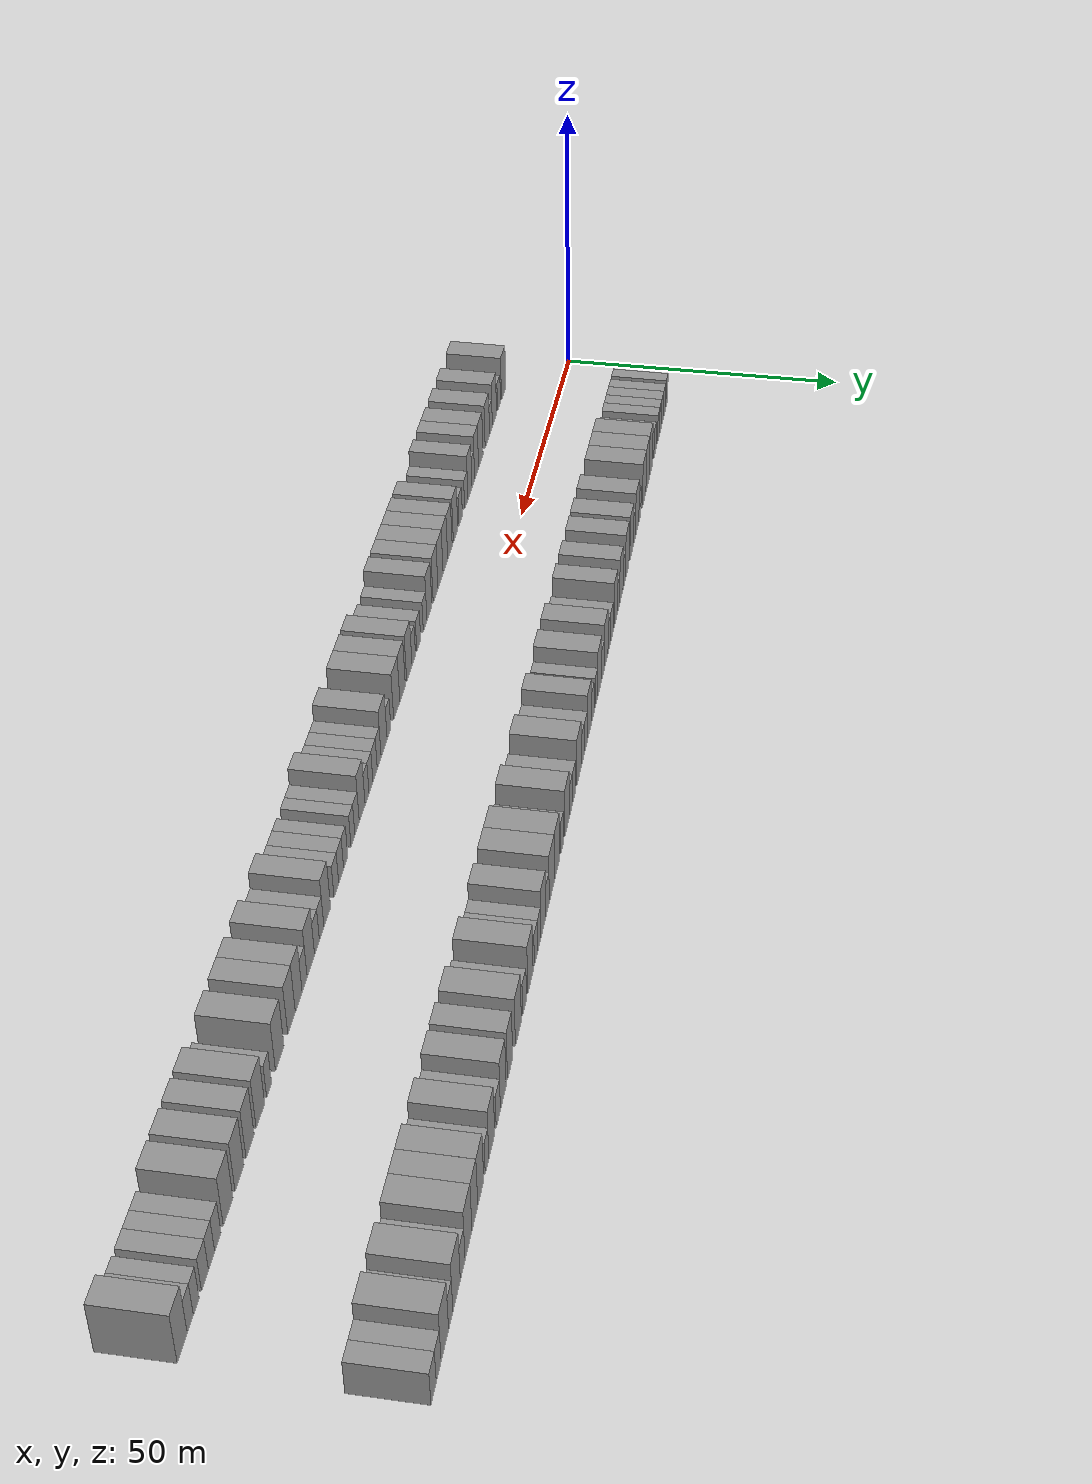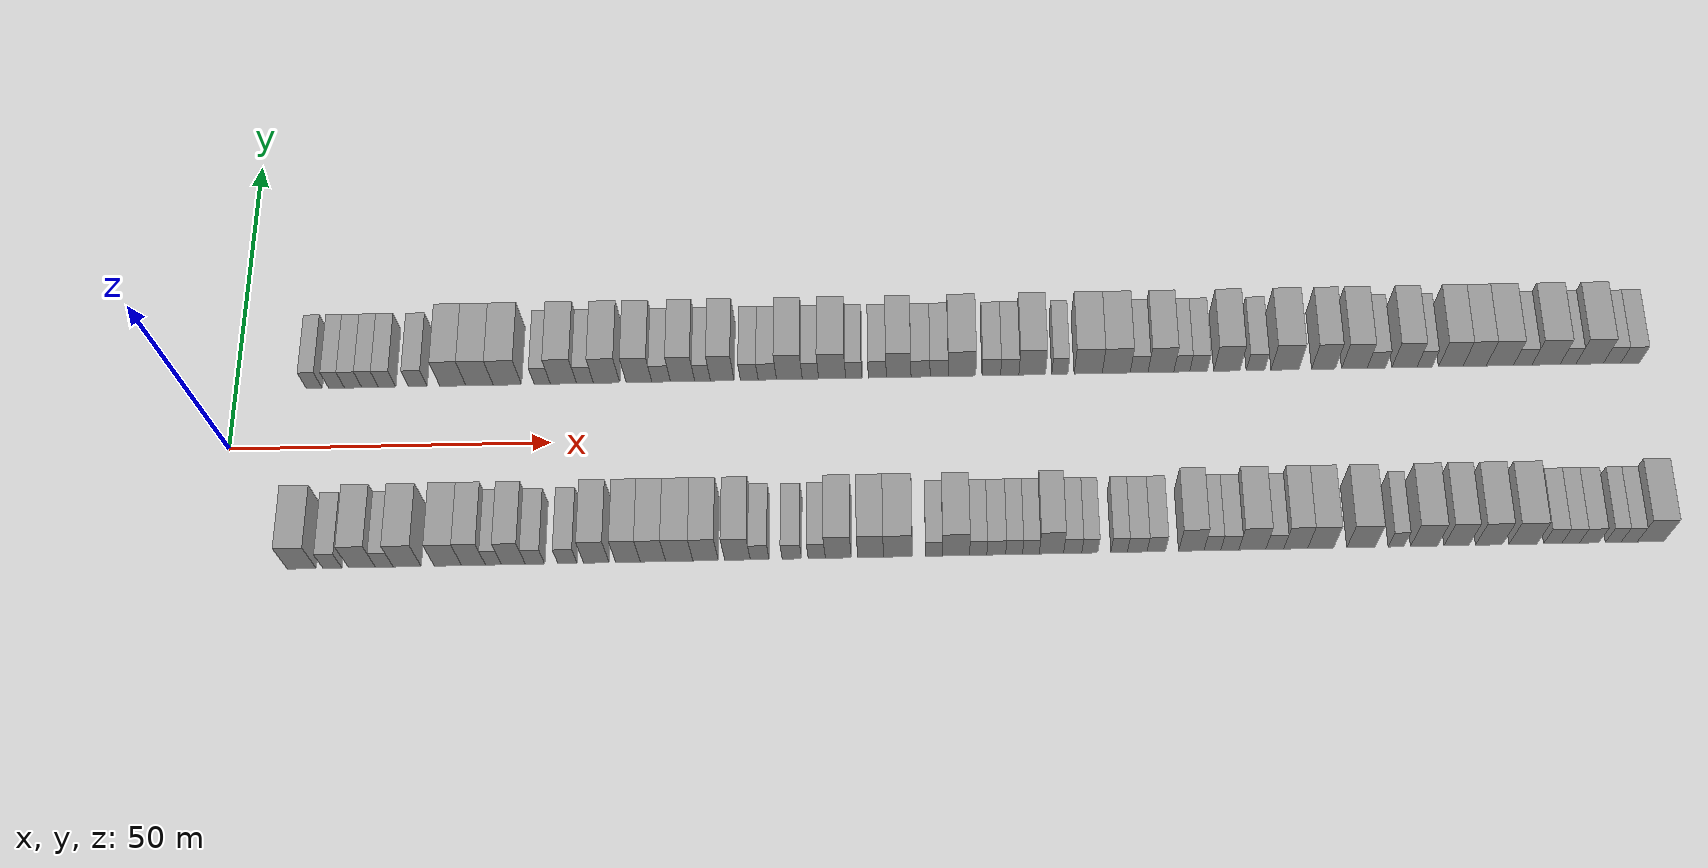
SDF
<sdf version="1.6">
 <world name="default">
  <scene>
   <sky><clouds><speed>12</speed></clouds></sky>
   <ambient>0.4 0.4 0.4 1</ambient>
   <background>0.7 0.7 0.7 1</background>
   <shadows>1</shadows>
  </scene>
  <gravity>0 0 -9.8066</gravity>
  <magnetic_field>6e-06 2.3e-05 -4.2e-05</magnetic_field>
  <physics default="0" name="default_physics" type="ode">
   <ode>
    <solver>
     <type>quick</type>
     <iters>10</iters>
     <sor>1.0</sor>
     <use_dynamic_moi_rescaling>0</use_dynamic_moi_rescaling>
    </solver>
    <constraints>
     <cfm>0</cfm>
     <erp>0.2</erp>
     <contact_max_correcting_vel>100</contact_max_correcting_vel>
     <contact_surface_layer>0.001</contact_surface_layer>
    </constraints>
   </ode>
   <max_step_size>0.004</max_step_size>
   <real_time_factor>1</real_time_factor>
   <real_time_update_rate>250</real_time_update_rate>
  </physics>
  <light name="sun" type="directional">
   <pose>0 0 10 0 0 0</pose>
   <diffuse>0.8 0.8 0.8 1</diffuse>
   <specular>0.2 0.2 0.2 1</specular>
   <attenuation>
    <range>1000</range>
    <constant>0.9</constant>
    <linear>0.01</linear>
    <quadratic>0.001</quadratic>
   </attenuation>
   <direction>-0.5 0.1 -0.9</direction>
  </light>
  <model name="building_1">
   <static>1</static>
   <pose>12.2512 15.0000 0 0.000000 0.000000 1.570796</pose>
   <link name="link">
    <pose>0 0 3.00 0 0 0</pose>
    <collision name="collision"><geometry><box><size>10.0000 2.5024 6.0000</size></box></geometry></collision>
    <visual name="visual">
     <cast_shadows>0</cast_shadows>
     <geometry><box><size>10.0000 2.5024 6.0000</size></box></geometry>
     <material>
      <script>
       <uri>model://grey_wall/materials/scripts</uri>
       <uri>model://grey_wall/materials/textures</uri>
       <name>vrc/grey_wall</name>
      </script>
     </material>
    </visual>
   </link>
  </model>
  <model name="building_2">
   <static>1</static>
   <pose>15.7438 15.0000 0 0.000000 0.000000 1.570796</pose>
   <link name="link">
    <pose>0 0 3.00 0 0 0</pose>
    <collision name="collision"><geometry><box><size>10.0000 2.4828 6.0000</size></box></geometry></collision>
    <visual name="visual">
     <cast_shadows>0</cast_shadows>
     <geometry><box><size>10.0000 2.4828 6.0000</size></box></geometry>
     <material>
      <script>
       <uri>model://grey_wall/materials/scripts</uri>
       <uri>model://grey_wall/materials/textures</uri>
       <name>vrc/grey_wall</name>
      </script>
     </material>
    </visual>
   </link>
  </model>
  <model name="building_3">
   <static>1</static>
   <pose>18.3443 15.0000 0 0.000000 0.000000 1.570796</pose>
   <link name="link">
    <pose>0 0 3.00 0 0 0</pose>
    <collision name="collision"><geometry><box><size>10.0000 2.7182 6.0000</size></box></geometry></collision>
    <visual name="visual">
     <cast_shadows>0</cast_shadows>
     <geometry><box><size>10.0000 2.7182 6.0000</size></box></geometry>
     <material>
      <script>
       <uri>model://grey_wall/materials/scripts</uri>
       <uri>model://grey_wall/materials/textures</uri>
       <name>vrc/grey_wall</name>
      </script>
     </material>
    </visual>
   </link>
  </model>
  <model name="building_4">
   <static>1</static>
   <pose>21.0118 15.0000 0 0.000000 0.000000 1.570796</pose>
   <link name="link">
    <pose>0 0 3.00 0 0 0</pose>
    <collision name="collision"><geometry><box><size>10.0000 2.6168 6.0000</size></box></geometry></collision>
    <visual name="visual">
     <cast_shadows>0</cast_shadows>
     <geometry><box><size>10.0000 2.6168 6.0000</size></box></geometry>
     <material>
      <script>
       <uri>model://grey_wall/materials/scripts</uri>
       <uri>model://grey_wall/materials/textures</uri>
       <name>vrc/grey_wall</name>
      </script>
     </material>
    </visual>
   </link>
  </model>
  <model name="building_5">
   <static>1</static>
   <pose>23.6738 15.0000 0 0.000000 0.000000 1.570796</pose>
   <link name="link">
    <pose>0 0 3.00 0 0 0</pose>
    <collision name="collision"><geometry><box><size>10.0000 2.7073 6.0000</size></box></geometry></collision>
    <visual name="visual">
     <cast_shadows>0</cast_shadows>
     <geometry><box><size>10.0000 2.7073 6.0000</size></box></geometry>
     <material>
      <script>
       <uri>model://grey_wall/materials/scripts</uri>
       <uri>model://grey_wall/materials/textures</uri>
       <name>vrc/grey_wall</name>
      </script>
     </material>
    </visual>
   </link>
  </model>
  <model name="building_6">
   <static>1</static>
   <pose>28.4945 15.0000 0 0.000000 0.000000 1.570796</pose>
   <link name="link">
    <pose>0 0 3.00 0 0 0</pose>
    <collision name="collision"><geometry><box><size>10.0000 2.9341 6.0000</size></box></geometry></collision>
    <visual name="visual">
     <cast_shadows>0</cast_shadows>
     <geometry><box><size>10.0000 2.9341 6.0000</size></box></geometry>
     <material>
      <script>
       <uri>model://grey_wall/materials/scripts</uri>
       <uri>model://grey_wall/materials/textures</uri>
       <name>vrc/grey_wall</name>
      </script>
     </material>
    </visual>
   </link>
  </model>
  <model name="building_7">
   <static>1</static>
   <pose>34.0111 15.0000 0 0.000000 0.000000 1.570796</pose>
   <link name="link">
    <pose>0 0 4.50 0 0 0</pose>
    <collision name="collision"><geometry><box><size>10.0000 4.0992 9.0000</size></box></geometry></collision>
    <visual name="visual">
     <cast_shadows>0</cast_shadows>
     <geometry><box><size>10.0000 4.0992 9.0000</size></box></geometry>
     <material>
      <script>
       <uri>model://grey_wall/materials/scripts</uri>
       <uri>model://grey_wall/materials/textures</uri>
       <name>vrc/grey_wall</name>
      </script>
     </material>
    </visual>
   </link>
  </model>
  <model name="building_8">
   <static>1</static>
   <pose>38.2104 15.0000 0 0.000000 0.000000 1.570796</pose>
   <link name="link">
    <pose>0 0 4.50 0 0 0</pose>
    <collision name="collision"><geometry><box><size>10.0000 4.2993 9.0000</size></box></geometry></collision>
    <visual name="visual">
     <cast_shadows>0</cast_shadows>
     <geometry><box><size>10.0000 4.2993 9.0000</size></box></geometry>
     <material>
      <script>
       <uri>model://grey_wall/materials/scripts</uri>
       <uri>model://grey_wall/materials/textures</uri>
       <name>vrc/grey_wall</name>
      </script>
     </material>
    </visual>
   </link>
  </model>
  <model name="building_9">
   <static>1</static>
   <pose>42.5813 15.0000 0 0.000000 0.000000 1.570796</pose>
   <link name="link">
    <pose>0 0 4.50 0 0 0</pose>
    <collision name="collision"><geometry><box><size>10.0000 4.4426 9.0000</size></box></geometry></collision>
    <visual name="visual">
     <cast_shadows>0</cast_shadows>
     <geometry><box><size>10.0000 4.4426 9.0000</size></box></geometry>
     <material>
      <script>
       <uri>model://grey_wall/materials/scripts</uri>
       <uri>model://grey_wall/materials/textures</uri>
       <name>vrc/grey_wall</name>
      </script>
     </material>
    </visual>
   </link>
  </model>
  <model name="building_10">
   <static>1</static>
   <pose>48.0679 15.0000 0 0.000000 0.000000 1.570796</pose>
   <link name="link">
    <pose>0 0 3.00 0 0 0</pose>
    <collision name="collision"><geometry><box><size>10.0000 2.5305 6.0000</size></box></geometry></collision>
    <visual name="visual">
     <cast_shadows>0</cast_shadows>
     <geometry><box><size>10.0000 2.5305 6.0000</size></box></geometry>
     <material>
      <script>
       <uri>model://grey_wall/materials/scripts</uri>
       <uri>model://grey_wall/materials/textures</uri>
       <name>vrc/grey_wall</name>
      </script>
     </material>
    </visual>
   </link>
  </model>
  <model name="building_11">
   <static>1</static>
   <pose>51.3964 15.0000 0 0.000000 0.000000 1.570796</pose>
   <link name="link">
    <pose>0 0 4.50 0 0 0</pose>
    <collision name="collision"><geometry><box><size>10.0000 4.1266 9.0000</size></box></geometry></collision>
    <visual name="visual">
     <cast_shadows>0</cast_shadows>
     <geometry><box><size>10.0000 4.1266 9.0000</size></box></geometry>
     <material>
      <script>
       <uri>model://grey_wall/materials/scripts</uri>
       <uri>model://grey_wall/materials/textures</uri>
       <name>vrc/grey_wall</name>
      </script>
     </material>
    </visual>
   </link>
  </model>
  <model name="building_12">
   <static>1</static>
   <pose>54.7969 15.0000 0 0.000000 0.000000 1.570796</pose>
   <link name="link">
    <pose>0 0 3.00 0 0 0</pose>
    <collision name="collision"><geometry><box><size>10.0000 2.6744 6.0000</size></box></geometry></collision>
    <visual name="visual">
     <cast_shadows>0</cast_shadows>
     <geometry><box><size>10.0000 2.6744 6.0000</size></box></geometry>
     <material>
      <script>
       <uri>model://grey_wall/materials/scripts</uri>
       <uri>model://grey_wall/materials/textures</uri>
       <name>vrc/grey_wall</name>
      </script>
     </material>
    </visual>
   </link>
  </model>
  <model name="building_13">
   <static>1</static>
   <pose>58.2003 15.0000 0 0.000000 0.000000 1.570796</pose>
   <link name="link">
    <pose>0 0 4.50 0 0 0</pose>
    <collision name="collision"><geometry><box><size>10.0000 4.1324 9.0000</size></box></geometry></collision>
    <visual name="visual">
     <cast_shadows>0</cast_shadows>
     <geometry><box><size>10.0000 4.1324 9.0000</size></box></geometry>
     <material>
      <script>
       <uri>model://grey_wall/materials/scripts</uri>
       <uri>model://grey_wall/materials/textures</uri>
       <name>vrc/grey_wall</name>
      </script>
     </material>
    </visual>
   </link>
  </model>
  <model name="building_14">
   <static>1</static>
   <pose>63.2929 15.0000 0 0.000000 0.000000 1.570796</pose>
   <link name="link">
    <pose>0 0 4.50 0 0 0</pose>
    <collision name="collision"><geometry><box><size>10.0000 4.0527 9.0000</size></box></geometry></collision>
    <visual name="visual">
     <cast_shadows>0</cast_shadows>
     <geometry><box><size>10.0000 4.0527 9.0000</size></box></geometry>
     <material>
      <script>
       <uri>model://grey_wall/materials/scripts</uri>
       <uri>model://grey_wall/materials/textures</uri>
       <name>vrc/grey_wall</name>
      </script>
     </material>
    </visual>
   </link>
  </model>
  <model name="building_15">
   <static>1</static>
   <pose>66.7770 15.0000 0 0.000000 0.000000 1.570796</pose>
   <link name="link">
    <pose>0 0 3.00 0 0 0</pose>
    <collision name="collision"><geometry><box><size>10.0000 2.9155 6.0000</size></box></geometry></collision>
    <visual name="visual">
     <cast_shadows>0</cast_shadows>
     <geometry><box><size>10.0000 2.9155 6.0000</size></box></geometry>
     <material>
      <script>
       <uri>model://grey_wall/materials/scripts</uri>
       <uri>model://grey_wall/materials/textures</uri>
       <name>vrc/grey_wall</name>
      </script>
     </material>
    </visual>
   </link>
  </model>
  <model name="building_16">
   <static>1</static>
   <pose>70.1506 15.0000 0 0.000000 0.000000 1.570796</pose>
   <link name="link">
    <pose>0 0 4.50 0 0 0</pose>
    <collision name="collision"><geometry><box><size>10.0000 3.8317 9.0000</size></box></geometry></collision>
    <visual name="visual">
     <cast_shadows>0</cast_shadows>
     <geometry><box><size>10.0000 3.8317 9.0000</size></box></geometry>
     <material>
      <script>
       <uri>model://grey_wall/materials/scripts</uri>
       <uri>model://grey_wall/materials/textures</uri>
       <name>vrc/grey_wall</name>
      </script>
     </material>
    </visual>
   </link>
  </model>
  <model name="building_17">
   <static>1</static>
   <pose>73.3016 15.0000 0 0.000000 0.000000 1.570796</pose>
   <link name="link">
    <pose>0 0 3.00 0 0 0</pose>
    <collision name="collision"><geometry><box><size>10.0000 2.4702 6.0000</size></box></geometry></collision>
    <visual name="visual">
     <cast_shadows>0</cast_shadows>
     <geometry><box><size>10.0000 2.4702 6.0000</size></box></geometry>
     <material>
      <script>
       <uri>model://grey_wall/materials/scripts</uri>
       <uri>model://grey_wall/materials/textures</uri>
       <name>vrc/grey_wall</name>
      </script>
     </material>
    </visual>
   </link>
  </model>
  <model name="building_18">
   <static>1</static>
   <pose>76.4071 15.0000 0 0.000000 0.000000 1.570796</pose>
   <link name="link">
    <pose>0 0 4.50 0 0 0</pose>
    <collision name="collision"><geometry><box><size>10.0000 3.7410 9.0000</size></box></geometry></collision>
    <visual name="visual">
     <cast_shadows>0</cast_shadows>
     <geometry><box><size>10.0000 3.7410 9.0000</size></box></geometry>
     <material>
      <script>
       <uri>model://grey_wall/materials/scripts</uri>
       <uri>model://grey_wall/materials/textures</uri>
       <name>vrc/grey_wall</name>
      </script>
     </material>
    </visual>
   </link>
  </model>
  <model name="building_19">
   <static>1</static>
   <pose>80.6656 15.0000 0 0.000000 0.000000 1.570796</pose>
   <link name="link">
    <pose>0 0 3.00 0 0 0</pose>
    <collision name="collision"><geometry><box><size>10.0000 2.7760 6.0000</size></box></geometry></collision>
    <visual name="visual">
     <cast_shadows>0</cast_shadows>
     <geometry><box><size>10.0000 2.7760 6.0000</size></box></geometry>
     <material>
      <script>
       <uri>model://grey_wall/materials/scripts</uri>
       <uri>model://grey_wall/materials/textures</uri>
       <name>vrc/grey_wall</name>
      </script>
     </material>
    </visual>
   </link>
  </model>
  <model name="building_20">
   <static>1</static>
   <pose>83.5055 15.0000 0 0.000000 0.000000 1.570796</pose>
   <link name="link">
    <pose>0 0 3.00 0 0 0</pose>
    <collision name="collision"><geometry><box><size>10.0000 2.9038 6.0000</size></box></geometry></collision>
    <visual name="visual">
     <cast_shadows>0</cast_shadows>
     <geometry><box><size>10.0000 2.9038 6.0000</size></box></geometry>
     <material>
      <script>
       <uri>model://grey_wall/materials/scripts</uri>
       <uri>model://grey_wall/materials/textures</uri>
       <name>vrc/grey_wall</name>
      </script>
     </material>
    </visual>
   </link>
  </model>
  <model name="building_21">
   <static>1</static>
   <pose>86.9885 15.0000 0 0.000000 0.000000 1.570796</pose>
   <link name="link">
    <pose>0 0 4.50 0 0 0</pose>
    <collision name="collision"><geometry><box><size>10.0000 4.0622 9.0000</size></box></geometry></collision>
    <visual name="visual">
     <cast_shadows>0</cast_shadows>
     <geometry><box><size>10.0000 4.0622 9.0000</size></box></geometry>
     <material>
      <script>
       <uri>model://grey_wall/materials/scripts</uri>
       <uri>model://grey_wall/materials/textures</uri>
       <name>vrc/grey_wall</name>
      </script>
     </material>
    </visual>
   </link>
  </model>
  <model name="building_22">
   <static>1</static>
   <pose>90.3040 15.0000 0 0.000000 0.000000 1.570796</pose>
   <link name="link">
    <pose>0 0 3.00 0 0 0</pose>
    <collision name="collision"><geometry><box><size>10.0000 2.5687 6.0000</size></box></geometry></collision>
    <visual name="visual">
     <cast_shadows>0</cast_shadows>
     <geometry><box><size>10.0000 2.5687 6.0000</size></box></geometry>
     <material>
      <script>
       <uri>model://grey_wall/materials/scripts</uri>
       <uri>model://grey_wall/materials/textures</uri>
       <name>vrc/grey_wall</name>
      </script>
     </material>
    </visual>
   </link>
  </model>
  <model name="building_23">
   <static>1</static>
   <pose>93.7211 15.0000 0 0.000000 0.000000 1.570796</pose>
   <link name="link">
    <pose>0 0 4.50 0 0 0</pose>
    <collision name="collision"><geometry><box><size>10.0000 4.2655 9.0000</size></box></geometry></collision>
    <visual name="visual">
     <cast_shadows>0</cast_shadows>
     <geometry><box><size>10.0000 4.2655 9.0000</size></box></geometry>
     <material>
      <script>
       <uri>model://grey_wall/materials/scripts</uri>
       <uri>model://grey_wall/materials/textures</uri>
       <name>vrc/grey_wall</name>
      </script>
     </material>
    </visual>
   </link>
  </model>
  <model name="building_24">
   <static>1</static>
   <pose>97.1481 15.0000 0 0.000000 0.000000 1.570796</pose>
   <link name="link">
    <pose>0 0 3.00 0 0 0</pose>
    <collision name="collision"><geometry><box><size>10.0000 2.5886 6.0000</size></box></geometry></collision>
    <visual name="visual">
     <cast_shadows>0</cast_shadows>
     <geometry><box><size>10.0000 2.5886 6.0000</size></box></geometry>
     <material>
      <script>
       <uri>model://grey_wall/materials/scripts</uri>
       <uri>model://grey_wall/materials/textures</uri>
       <name>vrc/grey_wall</name>
      </script>
     </material>
    </visual>
   </link>
  </model>
  <model name="building_25">
   <static>1</static>
   <pose>100.8649 15.0000 0 0.000000 0.000000 1.570796</pose>
   <link name="link">
    <pose>0 0 3.00 0 0 0</pose>
    <collision name="collision"><geometry><box><size>10.0000 2.8450 6.0000</size></box></geometry></collision>
    <visual name="visual">
     <cast_shadows>0</cast_shadows>
     <geometry><box><size>10.0000 2.8450 6.0000</size></box></geometry>
     <material>
      <script>
       <uri>model://grey_wall/materials/scripts</uri>
       <uri>model://grey_wall/materials/textures</uri>
       <name>vrc/grey_wall</name>
      </script>
     </material>
    </visual>
   </link>
  </model>
  <model name="building_26">
   <static>1</static>
   <pose>104.2250 15.0000 0 0.000000 0.000000 1.570796</pose>
   <link name="link">
    <pose>0 0 4.50 0 0 0</pose>
    <collision name="collision"><geometry><box><size>10.0000 3.8752 9.0000</size></box></geometry></collision>
    <visual name="visual">
     <cast_shadows>0</cast_shadows>
     <geometry><box><size>10.0000 3.8752 9.0000</size></box></geometry>
     <material>
      <script>
       <uri>model://grey_wall/materials/scripts</uri>
       <uri>model://grey_wall/materials/textures</uri>
       <name>vrc/grey_wall</name>
      </script>
     </material>
    </visual>
   </link>
  </model>
  <model name="building_27">
   <static>1</static>
   <pose>107.6613 15.0000 0 0.000000 0.000000 1.570796</pose>
   <link name="link">
    <pose>0 0 3.00 0 0 0</pose>
    <collision name="collision"><geometry><box><size>10.0000 2.9974 6.0000</size></box></geometry></collision>
    <visual name="visual">
     <cast_shadows>0</cast_shadows>
     <geometry><box><size>10.0000 2.9974 6.0000</size></box></geometry>
     <material>
      <script>
       <uri>model://grey_wall/materials/scripts</uri>
       <uri>model://grey_wall/materials/textures</uri>
       <name>vrc/grey_wall</name>
      </script>
     </material>
    </visual>
   </link>
  </model>
  <model name="building_28">
   <static>1</static>
   <pose>110.5838 15.0000 0 0.000000 0.000000 1.570796</pose>
   <link name="link">
    <pose>0 0 3.00 0 0 0</pose>
    <collision name="collision"><geometry><box><size>10.0000 2.8476 6.0000</size></box></geometry></collision>
    <visual name="visual">
     <cast_shadows>0</cast_shadows>
     <geometry><box><size>10.0000 2.8476 6.0000</size></box></geometry>
     <material>
      <script>
       <uri>model://grey_wall/materials/scripts</uri>
       <uri>model://grey_wall/materials/textures</uri>
       <name>vrc/grey_wall</name>
      </script>
     </material>
    </visual>
   </link>
  </model>
  <model name="building_29">
   <static>1</static>
   <pose>114.1921 15.0000 0 0.000000 0.000000 1.570796</pose>
   <link name="link">
    <pose>0 0 4.50 0 0 0</pose>
    <collision name="collision"><geometry><box><size>10.0000 4.3690 9.0000</size></box></geometry></collision>
    <visual name="visual">
     <cast_shadows>0</cast_shadows>
     <geometry><box><size>10.0000 4.3690 9.0000</size></box></geometry>
     <material>
      <script>
       <uri>model://grey_wall/materials/scripts</uri>
       <uri>model://grey_wall/materials/textures</uri>
       <name>vrc/grey_wall</name>
      </script>
     </material>
    </visual>
   </link>
  </model>
  <model name="building_30">
   <static>1</static>
   <pose>118.8395 15.0000 0 0.000000 0.000000 1.570796</pose>
   <link name="link">
    <pose>0 0 3.00 0 0 0</pose>
    <collision name="collision"><geometry><box><size>10.0000 2.9260 6.0000</size></box></geometry></collision>
    <visual name="visual">
     <cast_shadows>0</cast_shadows>
     <geometry><box><size>10.0000 2.9260 6.0000</size></box></geometry>
     <material>
      <script>
       <uri>model://grey_wall/materials/scripts</uri>
       <uri>model://grey_wall/materials/textures</uri>
       <name>vrc/grey_wall</name>
      </script>
     </material>
    </visual>
   </link>
  </model>
  <model name="building_31">
   <static>1</static>
   <pose>121.7471 15.0000 0 0.000000 0.000000 1.570796</pose>
   <link name="link">
    <pose>0 0 3.00 0 0 0</pose>
    <collision name="collision"><geometry><box><size>10.0000 2.8892 6.0000</size></box></geometry></collision>
    <visual name="visual">
     <cast_shadows>0</cast_shadows>
     <geometry><box><size>10.0000 2.8892 6.0000</size></box></geometry>
     <material>
      <script>
       <uri>model://grey_wall/materials/scripts</uri>
       <uri>model://grey_wall/materials/textures</uri>
       <name>vrc/grey_wall</name>
      </script>
     </material>
    </visual>
   </link>
  </model>
  <model name="building_32">
   <static>1</static>
   <pose>125.2870 15.0000 0 0.000000 0.000000 1.570796</pose>
   <link name="link">
    <pose>0 0 4.50 0 0 0</pose>
    <collision name="collision"><geometry><box><size>10.0000 4.1906 9.0000</size></box></geometry></collision>
    <visual name="visual">
     <cast_shadows>0</cast_shadows>
     <geometry><box><size>10.0000 4.1906 9.0000</size></box></geometry>
     <material>
      <script>
       <uri>model://grey_wall/materials/scripts</uri>
       <uri>model://grey_wall/materials/textures</uri>
       <name>vrc/grey_wall</name>
      </script>
     </material>
    </visual>
   </link>
  </model>
  <model name="building_33">
   <static>1</static>
   <pose>129.6487 15.0000 0 0.000000 0.000000 1.570796</pose>
   <link name="link">
    <pose>0 0 3.00 0 0 0</pose>
    <collision name="collision"><geometry><box><size>10.0000 2.5326 6.0000</size></box></geometry></collision>
    <visual name="visual">
     <cast_shadows>0</cast_shadows>
     <geometry><box><size>10.0000 2.5326 6.0000</size></box></geometry>
     <material>
      <script>
       <uri>model://grey_wall/materials/scripts</uri>
       <uri>model://grey_wall/materials/textures</uri>
       <name>vrc/grey_wall</name>
      </script>
     </material>
    </visual>
   </link>
  </model>
  <model name="building_34">
   <static>1</static>
   <pose>134.1399 15.0000 0 0.000000 0.000000 1.570796</pose>
   <link name="link">
    <pose>0 0 4.50 0 0 0</pose>
    <collision name="collision"><geometry><box><size>10.0000 4.4499 9.0000</size></box></geometry></collision>
    <visual name="visual">
     <cast_shadows>0</cast_shadows>
     <geometry><box><size>10.0000 4.4499 9.0000</size></box></geometry>
     <material>
      <script>
       <uri>model://grey_wall/materials/scripts</uri>
       <uri>model://grey_wall/materials/textures</uri>
       <name>vrc/grey_wall</name>
      </script>
     </material>
    </visual>
   </link>
  </model>
  <model name="building_35">
   <static>1</static>
   <pose>138.5769 15.0000 0 0.000000 0.000000 1.570796</pose>
   <link name="link">
    <pose>0 0 4.50 0 0 0</pose>
    <collision name="collision"><geometry><box><size>10.0000 4.4240 9.0000</size></box></geometry></collision>
    <visual name="visual">
     <cast_shadows>0</cast_shadows>
     <geometry><box><size>10.0000 4.4240 9.0000</size></box></geometry>
     <material>
      <script>
       <uri>model://grey_wall/materials/scripts</uri>
       <uri>model://grey_wall/materials/textures</uri>
       <name>vrc/grey_wall</name>
      </script>
     </material>
    </visual>
   </link>
  </model>
  <model name="building_36">
   <static>1</static>
   <pose>142.1965 15.0000 0 0.000000 0.000000 1.570796</pose>
   <link name="link">
    <pose>0 0 3.00 0 0 0</pose>
    <collision name="collision"><geometry><box><size>10.0000 2.8153 6.0000</size></box></geometry></collision>
    <visual name="visual">
     <cast_shadows>0</cast_shadows>
     <geometry><box><size>10.0000 2.8153 6.0000</size></box></geometry>
     <material>
      <script>
       <uri>model://grey_wall/materials/scripts</uri>
       <uri>model://grey_wall/materials/textures</uri>
       <name>vrc/grey_wall</name>
      </script>
     </material>
    </visual>
   </link>
  </model>
  <model name="building_37">
   <static>1</static>
   <pose>145.6440 15.0000 0 0.000000 0.000000 1.570796</pose>
   <link name="link">
    <pose>0 0 4.50 0 0 0</pose>
    <collision name="collision"><geometry><box><size>10.0000 4.0796 9.0000</size></box></geometry></collision>
    <visual name="visual">
     <cast_shadows>0</cast_shadows>
     <geometry><box><size>10.0000 4.0796 9.0000</size></box></geometry>
     <material>
      <script>
       <uri>model://grey_wall/materials/scripts</uri>
       <uri>model://grey_wall/materials/textures</uri>
       <name>vrc/grey_wall</name>
      </script>
     </material>
    </visual>
   </link>
  </model>
  <model name="building_38">
   <static>1</static>
   <pose>148.9304 15.0000 0 0.000000 0.000000 1.570796</pose>
   <link name="link">
    <pose>0 0 3.00 0 0 0</pose>
    <collision name="collision"><geometry><box><size>10.0000 2.4932 6.0000</size></box></geometry></collision>
    <visual name="visual">
     <cast_shadows>0</cast_shadows>
     <geometry><box><size>10.0000 2.4932 6.0000</size></box></geometry>
     <material>
      <script>
       <uri>model://grey_wall/materials/scripts</uri>
       <uri>model://grey_wall/materials/textures</uri>
       <name>vrc/grey_wall</name>
      </script>
     </material>
    </visual>
   </link>
  </model>
  <model name="building_39">
   <static>1</static>
   <pose>151.5765 15.0000 0 0.000000 0.000000 1.570796</pose>
   <link name="link">
    <pose>0 0 3.00 0 0 0</pose>
    <collision name="collision"><geometry><box><size>10.0000 2.7991 6.0000</size></box></geometry></collision>
    <visual name="visual">
     <cast_shadows>0</cast_shadows>
     <geometry><box><size>10.0000 2.7991 6.0000</size></box></geometry>
     <material>
      <script>
       <uri>model://grey_wall/materials/scripts</uri>
       <uri>model://grey_wall/materials/textures</uri>
       <name>vrc/grey_wall</name>
      </script>
     </material>
    </visual>
   </link>
  </model>
  <model name="building_40">
   <static>1</static>
   <pose>156.0516 15.0000 0 0.000000 0.000000 1.570796</pose>
   <link name="link">
    <pose>0 0 4.50 0 0 0</pose>
    <collision name="collision"><geometry><box><size>10.0000 4.1510 9.0000</size></box></geometry></collision>
    <visual name="visual">
     <cast_shadows>0</cast_shadows>
     <geometry><box><size>10.0000 4.1510 9.0000</size></box></geometry>
     <material>
      <script>
       <uri>model://grey_wall/materials/scripts</uri>
       <uri>model://grey_wall/materials/textures</uri>
       <name>vrc/grey_wall</name>
      </script>
     </material>
    </visual>
   </link>
  </model>
  <model name="building_41">
   <static>1</static>
   <pose>160.5889 15.0000 0 0.000000 0.000000 1.570796</pose>
   <link name="link">
    <pose>0 0 3.00 0 0 0</pose>
    <collision name="collision"><geometry><box><size>10.0000 2.9237 6.0000</size></box></geometry></collision>
    <visual name="visual">
     <cast_shadows>0</cast_shadows>
     <geometry><box><size>10.0000 2.9237 6.0000</size></box></geometry>
     <material>
      <script>
       <uri>model://grey_wall/materials/scripts</uri>
       <uri>model://grey_wall/materials/textures</uri>
       <name>vrc/grey_wall</name>
      </script>
     </material>
    </visual>
   </link>
  </model>
  <model name="building_42">
   <static>1</static>
   <pose>165.2645 15.0000 0 0.000000 0.000000 1.570796</pose>
   <link name="link">
    <pose>0 0 4.50 0 0 0</pose>
    <collision name="collision"><geometry><box><size>10.0000 4.4274 9.0000</size></box></geometry></collision>
    <visual name="visual">
     <cast_shadows>0</cast_shadows>
     <geometry><box><size>10.0000 4.4274 9.0000</size></box></geometry>
     <material>
      <script>
       <uri>model://grey_wall/materials/scripts</uri>
       <uri>model://grey_wall/materials/textures</uri>
       <name>vrc/grey_wall</name>
      </script>
     </material>
    </visual>
   </link>
  </model>
  <model name="building_43">
   <static>1</static>
   <pose>171.3550 15.0000 0 0.000000 0.000000 1.570796</pose>
   <link name="link">
    <pose>0 0 4.50 0 0 0</pose>
    <collision name="collision"><geometry><box><size>10.0000 3.7536 9.0000</size></box></geometry></collision>
    <visual name="visual">
     <cast_shadows>0</cast_shadows>
     <geometry><box><size>10.0000 3.7536 9.0000</size></box></geometry>
     <material>
      <script>
       <uri>model://grey_wall/materials/scripts</uri>
       <uri>model://grey_wall/materials/textures</uri>
       <name>vrc/grey_wall</name>
      </script>
     </material>
    </visual>
   </link>
  </model>
  <model name="building_44">
   <static>1</static>
   <pose>176.2489 15.0000 0 0.000000 0.000000 1.570796</pose>
   <link name="link">
    <pose>0 0 4.50 0 0 0</pose>
    <collision name="collision"><geometry><box><size>10.0000 4.0343 9.0000</size></box></geometry></collision>
    <visual name="visual">
     <cast_shadows>0</cast_shadows>
     <geometry><box><size>10.0000 4.0343 9.0000</size></box></geometry>
     <material>
      <script>
       <uri>model://grey_wall/materials/scripts</uri>
       <uri>model://grey_wall/materials/textures</uri>
       <name>vrc/grey_wall</name>
      </script>
     </material>
    </visual>
   </link>
  </model>
  <model name="building_45">
   <static>1</static>
   <pose>179.7240 15.0000 0 0.000000 0.000000 1.570796</pose>
   <link name="link">
    <pose>0 0 3.00 0 0 0</pose>
    <collision name="collision"><geometry><box><size>10.0000 2.9158 6.0000</size></box></geometry></collision>
    <visual name="visual">
     <cast_shadows>0</cast_shadows>
     <geometry><box><size>10.0000 2.9158 6.0000</size></box></geometry>
     <material>
      <script>
       <uri>model://grey_wall/materials/scripts</uri>
       <uri>model://grey_wall/materials/textures</uri>
       <name>vrc/grey_wall</name>
      </script>
     </material>
    </visual>
   </link>
  </model>
  <model name="building_46">
   <static>1</static>
   <pose>184.1755 15.0000 0 0.000000 0.000000 1.570796</pose>
   <link name="link">
    <pose>0 0 4.50 0 0 0</pose>
    <collision name="collision"><geometry><box><size>10.0000 3.9871 9.0000</size></box></geometry></collision>
    <visual name="visual">
     <cast_shadows>0</cast_shadows>
     <geometry><box><size>10.0000 3.9871 9.0000</size></box></geometry>
     <material>
      <script>
       <uri>model://grey_wall/materials/scripts</uri>
       <uri>model://grey_wall/materials/textures</uri>
       <name>vrc/grey_wall</name>
      </script>
     </material>
    </visual>
   </link>
  </model>
  <model name="building_47">
   <static>1</static>
   <pose>187.3735 15.0000 0 0.000000 0.000000 1.570796</pose>
   <link name="link">
    <pose>0 0 3.00 0 0 0</pose>
    <collision name="collision"><geometry><box><size>10.0000 2.4090 6.0000</size></box></geometry></collision>
    <visual name="visual">
     <cast_shadows>0</cast_shadows>
     <geometry><box><size>10.0000 2.4090 6.0000</size></box></geometry>
     <material>
      <script>
       <uri>model://grey_wall/materials/scripts</uri>
       <uri>model://grey_wall/materials/textures</uri>
       <name>vrc/grey_wall</name>
      </script>
     </material>
    </visual>
   </link>
  </model>
  <model name="building_48">
   <static>1</static>
   <pose>191.5131 15.0000 0 0.000000 0.000000 1.570796</pose>
   <link name="link">
    <pose>0 0 4.50 0 0 0</pose>
    <collision name="collision"><geometry><box><size>10.0000 3.8702 9.0000</size></box></geometry></collision>
    <visual name="visual">
     <cast_shadows>0</cast_shadows>
     <geometry><box><size>10.0000 3.8702 9.0000</size></box></geometry>
     <material>
      <script>
       <uri>model://grey_wall/materials/scripts</uri>
       <uri>model://grey_wall/materials/textures</uri>
       <name>vrc/grey_wall</name>
      </script>
     </material>
    </visual>
   </link>
  </model>
  <model name="building_49">
   <static>1</static>
   <pose>195.3071 15.0000 0 0.000000 0.000000 1.570796</pose>
   <link name="link">
    <pose>0 0 4.50 0 0 0</pose>
    <collision name="collision"><geometry><box><size>10.0000 3.7177 9.0000</size></box></geometry></collision>
    <visual name="visual">
     <cast_shadows>0</cast_shadows>
     <geometry><box><size>10.0000 3.7177 9.0000</size></box></geometry>
     <material>
      <script>
       <uri>model://grey_wall/materials/scripts</uri>
       <uri>model://grey_wall/materials/textures</uri>
       <name>vrc/grey_wall</name>
      </script>
     </material>
    </visual>
   </link>
  </model>
  <model name="building_50">
   <static>1</static>
   <pose>199.3210 15.0000 0 0.000000 0.000000 1.570796</pose>
   <link name="link">
    <pose>0 0 4.50 0 0 0</pose>
    <collision name="collision"><geometry><box><size>10.0000 4.3102 9.0000</size></box></geometry></collision>
    <visual name="visual">
     <cast_shadows>0</cast_shadows>
     <geometry><box><size>10.0000 4.3102 9.0000</size></box></geometry>
     <material>
      <script>
       <uri>model://grey_wall/materials/scripts</uri>
       <uri>model://grey_wall/materials/textures</uri>
       <name>vrc/grey_wall</name>
      </script>
     </material>
    </visual>
   </link>
  </model>
  <model name="building_51">
   <static>1</static>
   <pose>202.9413 15.0000 0 0.000000 0.000000 1.570796</pose>
   <link name="link">
    <pose>0 0 3.00 0 0 0</pose>
    <collision name="collision"><geometry><box><size>10.0000 2.9304 6.0000</size></box></geometry></collision>
    <visual name="visual">
     <cast_shadows>0</cast_shadows>
     <geometry><box><size>10.0000 2.9304 6.0000</size></box></geometry>
     <material>
      <script>
       <uri>model://grey_wall/materials/scripts</uri>
       <uri>model://grey_wall/materials/textures</uri>
       <name>vrc/grey_wall</name>
      </script>
     </material>
    </visual>
   </link>
  </model>
  <model name="building_52">
   <static>1</static>
   <pose>206.6378 15.0000 0 0.000000 0.000000 1.570796</pose>
   <link name="link">
    <pose>0 0 4.50 0 0 0</pose>
    <collision name="collision"><geometry><box><size>10.0000 4.4625 9.0000</size></box></geometry></collision>
    <visual name="visual">
     <cast_shadows>0</cast_shadows>
     <geometry><box><size>10.0000 4.4625 9.0000</size></box></geometry>
     <material>
      <script>
       <uri>model://grey_wall/materials/scripts</uri>
       <uri>model://grey_wall/materials/textures</uri>
       <name>vrc/grey_wall</name>
      </script>
     </material>
    </visual>
   </link>
  </model>
  <model name="building_53">
   <static>1</static>
   <pose>210.1238 15.0000 0 0.000000 0.000000 1.570796</pose>
   <link name="link">
    <pose>0 0 3.00 0 0 0</pose>
    <collision name="collision"><geometry><box><size>10.0000 2.5096 6.0000</size></box></geometry></collision>
    <visual name="visual">
     <cast_shadows>0</cast_shadows>
     <geometry><box><size>10.0000 2.5096 6.0000</size></box></geometry>
     <material>
      <script>
       <uri>model://grey_wall/materials/scripts</uri>
       <uri>model://grey_wall/materials/textures</uri>
       <name>vrc/grey_wall</name>
      </script>
     </material>
    </visual>
   </link>
  </model>
  <model name="building_54">
   <static>1</static>
   <pose>213.5482 15.0000 0 0.000000 0.000000 1.570796</pose>
   <link name="link">
    <pose>0 0 4.50 0 0 0</pose>
    <collision name="collision"><geometry><box><size>10.0000 4.3391 9.0000</size></box></geometry></collision>
    <visual name="visual">
     <cast_shadows>0</cast_shadows>
     <geometry><box><size>10.0000 4.3391 9.0000</size></box></geometry>
     <material>
      <script>
       <uri>model://grey_wall/materials/scripts</uri>
       <uri>model://grey_wall/materials/textures</uri>
       <name>vrc/grey_wall</name>
      </script>
     </material>
    </visual>
   </link>
  </model>
  <model name="building_55">
   <static>1</static>
   <pose>217.0966 15.0000 0 0.000000 0.000000 1.570796</pose>
   <link name="link">
    <pose>0 0 3.00 0 0 0</pose>
    <collision name="collision"><geometry><box><size>10.0000 2.7576 6.0000</size></box></geometry></collision>
    <visual name="visual">
     <cast_shadows>0</cast_shadows>
     <geometry><box><size>10.0000 2.7576 6.0000</size></box></geometry>
     <material>
      <script>
       <uri>model://grey_wall/materials/scripts</uri>
       <uri>model://grey_wall/materials/textures</uri>
       <name>vrc/grey_wall</name>
      </script>
     </material>
    </visual>
   </link>
  </model>
  <model name="building_56">
   <static>1</static>
   <pose>219.9685 15.0000 0 0.000000 0.000000 1.570796</pose>
   <link name="link">
    <pose>0 0 3.00 0 0 0</pose>
    <collision name="collision"><geometry><box><size>10.0000 2.9861 6.0000</size></box></geometry></collision>
    <visual name="visual">
     <cast_shadows>0</cast_shadows>
     <geometry><box><size>10.0000 2.9861 6.0000</size></box></geometry>
     <material>
      <script>
       <uri>model://grey_wall/materials/scripts</uri>
       <uri>model://grey_wall/materials/textures</uri>
       <name>vrc/grey_wall</name>
      </script>
     </material>
    </visual>
   </link>
  </model>
  <model name="building_57">
   <static>1</static>
   <pose>13.1892 -15.0000 0 0.000000 0.000000 1.570796</pose>
   <link name="link">
    <pose>0 0 4.50 0 0 0</pose>
    <collision name="collision"><geometry><box><size>10.0000 4.3785 9.0000</size></box></geometry></collision>
    <visual name="visual">
     <cast_shadows>0</cast_shadows>
     <geometry><box><size>10.0000 4.3785 9.0000</size></box></geometry>
     <material>
      <script>
       <uri>model://grey_wall/materials/scripts</uri>
       <uri>model://grey_wall/materials/textures</uri>
       <name>vrc/grey_wall</name>
      </script>
     </material>
    </visual>
   </link>
  </model>
  <model name="building_58">
   <static>1</static>
   <pose>17.8253 -15.0000 0 0.000000 0.000000 1.570796</pose>
   <link name="link">
    <pose>0 0 3.00 0 0 0</pose>
    <collision name="collision"><geometry><box><size>10.0000 2.8936 6.0000</size></box></geometry></collision>
    <visual name="visual">
     <cast_shadows>0</cast_shadows>
     <geometry><box><size>10.0000 2.8936 6.0000</size></box></geometry>
     <material>
      <script>
       <uri>model://grey_wall/materials/scripts</uri>
       <uri>model://grey_wall/materials/textures</uri>
       <name>vrc/grey_wall</name>
      </script>
     </material>
    </visual>
   </link>
  </model>
  <model name="building_59">
   <static>1</static>
   <pose>22.3184 -15.0000 0 0.000000 0.000000 1.570796</pose>
   <link name="link">
    <pose>0 0 4.50 0 0 0</pose>
    <collision name="collision"><geometry><box><size>10.0000 4.0927 9.0000</size></box></geometry></collision>
    <visual name="visual">
     <cast_shadows>0</cast_shadows>
     <geometry><box><size>10.0000 4.0927 9.0000</size></box></geometry>
     <material>
      <script>
       <uri>model://grey_wall/materials/scripts</uri>
       <uri>model://grey_wall/materials/textures</uri>
       <name>vrc/grey_wall</name>
      </script>
     </material>
    </visual>
   </link>
  </model>
  <model name="building_60">
   <static>1</static>
   <pose>25.7051 -15.0000 0 0.000000 0.000000 1.570796</pose>
   <link name="link">
    <pose>0 0 3.00 0 0 0</pose>
    <collision name="collision"><geometry><box><size>10.0000 2.6806 6.0000</size></box></geometry></collision>
    <visual name="visual">
     <cast_shadows>0</cast_shadows>
     <geometry><box><size>10.0000 2.6806 6.0000</size></box></geometry>
     <material>
      <script>
       <uri>model://grey_wall/materials/scripts</uri>
       <uri>model://grey_wall/materials/textures</uri>
       <name>vrc/grey_wall</name>
      </script>
     </material>
    </visual>
   </link>
  </model>
  <model name="building_61">
   <static>1</static>
   <pose>29.1625 -15.0000 0 0.000000 0.000000 1.570796</pose>
   <link name="link">
    <pose>0 0 4.50 0 0 0</pose>
    <collision name="collision"><geometry><box><size>10.0000 4.2343 9.0000</size></box></geometry></collision>
    <visual name="visual">
     <cast_shadows>0</cast_shadows>
     <geometry><box><size>10.0000 4.2343 9.0000</size></box></geometry>
     <material>
      <script>
       <uri>model://grey_wall/materials/scripts</uri>
       <uri>model://grey_wall/materials/textures</uri>
       <name>vrc/grey_wall</name>
      </script>
     </material>
    </visual>
   </link>
  </model>
  <model name="building_62">
   <static>1</static>
   <pose>35.3511 -15.0000 0 0.000000 0.000000 1.570796</pose>
   <link name="link">
    <pose>0 0 4.50 0 0 0</pose>
    <collision name="collision"><geometry><box><size>10.0000 4.1427 9.0000</size></box></geometry></collision>
    <visual name="visual">
     <cast_shadows>0</cast_shadows>
     <geometry><box><size>10.0000 4.1427 9.0000</size></box></geometry>
     <material>
      <script>
       <uri>model://grey_wall/materials/scripts</uri>
       <uri>model://grey_wall/materials/textures</uri>
       <name>vrc/grey_wall</name>
      </script>
     </material>
    </visual>
   </link>
  </model>
  <model name="building_63">
   <static>1</static>
   <pose>39.2301 -15.0000 0 0.000000 0.000000 1.570796</pose>
   <link name="link">
    <pose>0 0 4.50 0 0 0</pose>
    <collision name="collision"><geometry><box><size>10.0000 3.6155 9.0000</size></box></geometry></collision>
    <visual name="visual">
     <cast_shadows>0</cast_shadows>
     <geometry><box><size>10.0000 3.6155 9.0000</size></box></geometry>
     <material>
      <script>
       <uri>model://grey_wall/materials/scripts</uri>
       <uri>model://grey_wall/materials/textures</uri>
       <name>vrc/grey_wall</name>
      </script>
     </material>
    </visual>
   </link>
  </model>
  <model name="building_64">
   <static>1</static>
   <pose>42.2406 -15.0000 0 0.000000 0.000000 1.570796</pose>
   <link name="link">
    <pose>0 0 3.00 0 0 0</pose>
    <collision name="collision"><geometry><box><size>10.0000 2.4054 6.0000</size></box></geometry></collision>
    <visual name="visual">
     <cast_shadows>0</cast_shadows>
     <geometry><box><size>10.0000 2.4054 6.0000</size></box></geometry>
     <material>
      <script>
       <uri>model://grey_wall/materials/scripts</uri>
       <uri>model://grey_wall/materials/textures</uri>
       <name>vrc/grey_wall</name>
      </script>
     </material>
    </visual>
   </link>
  </model>
  <model name="building_65">
   <static>1</static>
   <pose>45.2627 -15.0000 0 0.000000 0.000000 1.570796</pose>
   <link name="link">
    <pose>0 0 4.50 0 0 0</pose>
    <collision name="collision"><geometry><box><size>10.0000 3.6388 9.0000</size></box></geometry></collision>
    <visual name="visual">
     <cast_shadows>0</cast_shadows>
     <geometry><box><size>10.0000 3.6388 9.0000</size></box></geometry>
     <material>
      <script>
       <uri>model://grey_wall/materials/scripts</uri>
       <uri>model://grey_wall/materials/textures</uri>
       <name>vrc/grey_wall</name>
      </script>
     </material>
    </visual>
   </link>
  </model>
  <model name="building_66">
   <static>1</static>
   <pose>48.5496 -15.0000 0 0.000000 0.000000 1.570796</pose>
   <link name="link">
    <pose>0 0 3.00 0 0 0</pose>
    <collision name="collision"><geometry><box><size>10.0000 2.9351 6.0000</size></box></geometry></collision>
    <visual name="visual">
     <cast_shadows>0</cast_shadows>
     <geometry><box><size>10.0000 2.9351 6.0000</size></box></geometry>
     <material>
      <script>
       <uri>model://grey_wall/materials/scripts</uri>
       <uri>model://grey_wall/materials/textures</uri>
       <name>vrc/grey_wall</name>
      </script>
     </material>
    </visual>
   </link>
  </model>
  <model name="building_67">
   <static>1</static>
   <pose>53.4762 -15.0000 0 0.000000 0.000000 1.570796</pose>
   <link name="link">
    <pose>0 0 3.00 0 0 0</pose>
    <collision name="collision"><geometry><box><size>10.0000 2.9179 6.0000</size></box></geometry></collision>
    <visual name="visual">
     <cast_shadows>0</cast_shadows>
     <geometry><box><size>10.0000 2.9179 6.0000</size></box></geometry>
     <material>
      <script>
       <uri>model://grey_wall/materials/scripts</uri>
       <uri>model://grey_wall/materials/textures</uri>
       <name>vrc/grey_wall</name>
      </script>
     </material>
    </visual>
   </link>
  </model>
  <model name="building_68">
   <static>1</static>
   <pose>57.8662 -15.0000 0 0.000000 0.000000 1.570796</pose>
   <link name="link">
    <pose>0 0 4.50 0 0 0</pose>
    <collision name="collision"><geometry><box><size>10.0000 3.8623 9.0000</size></box></geometry></collision>
    <visual name="visual">
     <cast_shadows>0</cast_shadows>
     <geometry><box><size>10.0000 3.8623 9.0000</size></box></geometry>
     <material>
      <script>
       <uri>model://grey_wall/materials/scripts</uri>
       <uri>model://grey_wall/materials/textures</uri>
       <name>vrc/grey_wall</name>
      </script>
     </material>
    </visual>
   </link>
  </model>
  <model name="building_69">
   <static>1</static>
   <pose>62.6625 -15.0000 0 0.000000 0.000000 1.570796</pose>
   <link name="link">
    <pose>0 0 4.50 0 0 0</pose>
    <collision name="collision"><geometry><box><size>10.0000 3.7303 9.0000</size></box></geometry></collision>
    <visual name="visual">
     <cast_shadows>0</cast_shadows>
     <geometry><box><size>10.0000 3.7303 9.0000</size></box></geometry>
     <material>
      <script>
       <uri>model://grey_wall/materials/scripts</uri>
       <uri>model://grey_wall/materials/textures</uri>
       <name>vrc/grey_wall</name>
      </script>
     </material>
    </visual>
   </link>
  </model>
  <model name="building_70">
   <static>1</static>
   <pose>66.4581 -15.0000 0 0.000000 0.000000 1.570796</pose>
   <link name="link">
    <pose>0 0 4.50 0 0 0</pose>
    <collision name="collision"><geometry><box><size>10.0000 3.8610 9.0000</size></box></geometry></collision>
    <visual name="visual">
     <cast_shadows>0</cast_shadows>
     <geometry><box><size>10.0000 3.8610 9.0000</size></box></geometry>
     <material>
      <script>
       <uri>model://grey_wall/materials/scripts</uri>
       <uri>model://grey_wall/materials/textures</uri>
       <name>vrc/grey_wall</name>
      </script>
     </material>
    </visual>
   </link>
  </model>
  <model name="building_71">
   <static>1</static>
   <pose>70.4553 -15.0000 0 0.000000 0.000000 1.570796</pose>
   <link name="link">
    <pose>0 0 4.50 0 0 0</pose>
    <collision name="collision"><geometry><box><size>10.0000 4.1333 9.0000</size></box></geometry></collision>
    <visual name="visual">
     <cast_shadows>0</cast_shadows>
     <geometry><box><size>10.0000 4.1333 9.0000</size></box></geometry>
     <material>
      <script>
       <uri>model://grey_wall/materials/scripts</uri>
       <uri>model://grey_wall/materials/textures</uri>
       <name>vrc/grey_wall</name>
      </script>
     </material>
    </visual>
   </link>
  </model>
  <model name="building_72">
   <static>1</static>
   <pose>74.4442 -15.0000 0 0.000000 0.000000 1.570796</pose>
   <link name="link">
    <pose>0 0 4.50 0 0 0</pose>
    <collision name="collision"><geometry><box><size>10.0000 3.8445 9.0000</size></box></geometry></collision>
    <visual name="visual">
     <cast_shadows>0</cast_shadows>
     <geometry><box><size>10.0000 3.8445 9.0000</size></box></geometry>
     <material>
      <script>
       <uri>model://grey_wall/materials/scripts</uri>
       <uri>model://grey_wall/materials/textures</uri>
       <name>vrc/grey_wall</name>
      </script>
     </material>
    </visual>
   </link>
  </model>
  <model name="building_73">
   <static>1</static>
   <pose>79.3001 -15.0000 0 0.000000 0.000000 1.570796</pose>
   <link name="link">
    <pose>0 0 4.50 0 0 0</pose>
    <collision name="collision"><geometry><box><size>10.0000 3.8674 9.0000</size></box></geometry></collision>
    <visual name="visual">
     <cast_shadows>0</cast_shadows>
     <geometry><box><size>10.0000 3.8674 9.0000</size></box></geometry>
     <material>
      <script>
       <uri>model://grey_wall/materials/scripts</uri>
       <uri>model://grey_wall/materials/textures</uri>
       <name>vrc/grey_wall</name>
      </script>
     </material>
    </visual>
   </link>
  </model>
  <model name="building_74">
   <static>1</static>
   <pose>82.6624 -15.0000 0 0.000000 0.000000 1.570796</pose>
   <link name="link">
    <pose>0 0 3.00 0 0 0</pose>
    <collision name="collision"><geometry><box><size>10.0000 2.8571 6.0000</size></box></geometry></collision>
    <visual name="visual">
     <cast_shadows>0</cast_shadows>
     <geometry><box><size>10.0000 2.8571 6.0000</size></box></geometry>
     <material>
      <script>
       <uri>model://grey_wall/materials/scripts</uri>
       <uri>model://grey_wall/materials/textures</uri>
       <name>vrc/grey_wall</name>
      </script>
     </material>
    </visual>
   </link>
  </model>
  <model name="building_75">
   <static>1</static>
   <pose>87.5683 -15.0000 0 0.000000 0.000000 1.570796</pose>
   <link name="link">
    <pose>0 0 3.00 0 0 0</pose>
    <collision name="collision"><geometry><box><size>10.0000 2.9547 6.0000</size></box></geometry></collision>
    <visual name="visual">
     <cast_shadows>0</cast_shadows>
     <geometry><box><size>10.0000 2.9547 6.0000</size></box></geometry>
     <material>
      <script>
       <uri>model://grey_wall/materials/scripts</uri>
       <uri>model://grey_wall/materials/textures</uri>
       <name>vrc/grey_wall</name>
      </script>
     </material>
    </visual>
   </link>
  </model>
  <model name="building_76">
   <static>1</static>
   <pose>91.3424 -15.0000 0 0.000000 0.000000 1.570796</pose>
   <link name="link">
    <pose>0 0 3.00 0 0 0</pose>
    <collision name="collision"><geometry><box><size>10.0000 2.5934 6.0000</size></box></geometry></collision>
    <visual name="visual">
     <cast_shadows>0</cast_shadows>
     <geometry><box><size>10.0000 2.5934 6.0000</size></box></geometry>
     <material>
      <script>
       <uri>model://grey_wall/materials/scripts</uri>
       <uri>model://grey_wall/materials/textures</uri>
       <name>vrc/grey_wall</name>
      </script>
     </material>
    </visual>
   </link>
  </model>
  <model name="building_77">
   <static>1</static>
   <pose>94.6153 -15.0000 0 0.000000 0.000000 1.570796</pose>
   <link name="link">
    <pose>0 0 4.50 0 0 0</pose>
    <collision name="collision"><geometry><box><size>10.0000 3.9525 9.0000</size></box></geometry></collision>
    <visual name="visual">
     <cast_shadows>0</cast_shadows>
     <geometry><box><size>10.0000 3.9525 9.0000</size></box></geometry>
     <material>
      <script>
       <uri>model://grey_wall/materials/scripts</uri>
       <uri>model://grey_wall/materials/textures</uri>
       <name>vrc/grey_wall</name>
      </script>
     </material>
    </visual>
   </link>
  </model>
  <model name="building_78">
   <static>1</static>
   <pose>99.5565 -15.0000 0 0.000000 0.000000 1.570796</pose>
   <link name="link">
    <pose>0 0 4.50 0 0 0</pose>
    <collision name="collision"><geometry><box><size>10.0000 3.9299 9.0000</size></box></geometry></collision>
    <visual name="visual">
     <cast_shadows>0</cast_shadows>
     <geometry><box><size>10.0000 3.9299 9.0000</size></box></geometry>
     <material>
      <script>
       <uri>model://grey_wall/materials/scripts</uri>
       <uri>model://grey_wall/materials/textures</uri>
       <name>vrc/grey_wall</name>
      </script>
     </material>
    </visual>
   </link>
  </model>
  <model name="building_79">
   <static>1</static>
   <pose>103.7073 -15.0000 0 0.000000 0.000000 1.570796</pose>
   <link name="link">
    <pose>0 0 4.50 0 0 0</pose>
    <collision name="collision"><geometry><box><size>10.0000 4.3716 9.0000</size></box></geometry></collision>
    <visual name="visual">
     <cast_shadows>0</cast_shadows>
     <geometry><box><size>10.0000 4.3716 9.0000</size></box></geometry>
     <material>
      <script>
       <uri>model://grey_wall/materials/scripts</uri>
       <uri>model://grey_wall/materials/textures</uri>
       <name>vrc/grey_wall</name>
      </script>
     </material>
    </visual>
   </link>
  </model>
  <model name="building_80">
   <static>1</static>
   <pose>109.1833 -15.0000 0 0.000000 0.000000 1.570796</pose>
   <link name="link">
    <pose>0 0 3.00 0 0 0</pose>
    <collision name="collision"><geometry><box><size>10.0000 2.5805 6.0000</size></box></geometry></collision>
    <visual name="visual">
     <cast_shadows>0</cast_shadows>
     <geometry><box><size>10.0000 2.5805 6.0000</size></box></geometry>
     <material>
      <script>
       <uri>model://grey_wall/materials/scripts</uri>
       <uri>model://grey_wall/materials/textures</uri>
       <name>vrc/grey_wall</name>
      </script>
     </material>
    </visual>
   </link>
  </model>
  <model name="building_81">
   <static>1</static>
   <pose>112.5316 -15.0000 0 0.000000 0.000000 1.570796</pose>
   <link name="link">
    <pose>0 0 4.50 0 0 0</pose>
    <collision name="collision"><geometry><box><size>10.0000 4.1161 9.0000</size></box></geometry></collision>
    <visual name="visual">
     <cast_shadows>0</cast_shadows>
     <geometry><box><size>10.0000 4.1161 9.0000</size></box></geometry>
     <material>
      <script>
       <uri>model://grey_wall/materials/scripts</uri>
       <uri>model://grey_wall/materials/textures</uri>
       <name>vrc/grey_wall</name>
      </script>
     </material>
    </visual>
   </link>
  </model>
  <model name="building_82">
   <static>1</static>
   <pose>115.8994 -15.0000 0 0.000000 0.000000 1.570796</pose>
   <link name="link">
    <pose>0 0 3.00 0 0 0</pose>
    <collision name="collision"><geometry><box><size>10.0000 2.6196 6.0000</size></box></geometry></collision>
    <visual name="visual">
     <cast_shadows>0</cast_shadows>
     <geometry><box><size>10.0000 2.6196 6.0000</size></box></geometry>
     <material>
      <script>
       <uri>model://grey_wall/materials/scripts</uri>
       <uri>model://grey_wall/materials/textures</uri>
       <name>vrc/grey_wall</name>
      </script>
     </material>
    </visual>
   </link>
  </model>
  <model name="building_83">
   <static>1</static>
   <pose>118.6435 -15.0000 0 0.000000 0.000000 1.570796</pose>
   <link name="link">
    <pose>0 0 3.00 0 0 0</pose>
    <collision name="collision"><geometry><box><size>10.0000 2.8686 6.0000</size></box></geometry></collision>
    <visual name="visual">
     <cast_shadows>0</cast_shadows>
     <geometry><box><size>10.0000 2.8686 6.0000</size></box></geometry>
     <material>
      <script>
       <uri>model://grey_wall/materials/scripts</uri>
       <uri>model://grey_wall/materials/textures</uri>
       <name>vrc/grey_wall</name>
      </script>
     </material>
    </visual>
   </link>
  </model>
  <model name="building_84">
   <static>1</static>
   <pose>121.3555 -15.0000 0 0.000000 0.000000 1.570796</pose>
   <link name="link">
    <pose>0 0 3.00 0 0 0</pose>
    <collision name="collision"><geometry><box><size>10.0000 2.5554 6.0000</size></box></geometry></collision>
    <visual name="visual">
     <cast_shadows>0</cast_shadows>
     <geometry><box><size>10.0000 2.5554 6.0000</size></box></geometry>
     <material>
      <script>
       <uri>model://grey_wall/materials/scripts</uri>
       <uri>model://grey_wall/materials/textures</uri>
       <name>vrc/grey_wall</name>
      </script>
     </material>
    </visual>
   </link>
  </model>
  <model name="building_85">
   <static>1</static>
   <pose>123.9093 -15.0000 0 0.000000 0.000000 1.570796</pose>
   <link name="link">
    <pose>0 0 3.00 0 0 0</pose>
    <collision name="collision"><geometry><box><size>10.0000 2.5523 6.0000</size></box></geometry></collision>
    <visual name="visual">
     <cast_shadows>0</cast_shadows>
     <geometry><box><size>10.0000 2.5523 6.0000</size></box></geometry>
     <material>
      <script>
       <uri>model://grey_wall/materials/scripts</uri>
       <uri>model://grey_wall/materials/textures</uri>
       <name>vrc/grey_wall</name>
      </script>
     </material>
    </visual>
   </link>
  </model>
  <model name="building_86">
   <static>1</static>
   <pose>127.0417 -15.0000 0 0.000000 0.000000 1.570796</pose>
   <link name="link">
    <pose>0 0 4.50 0 0 0</pose>
    <collision name="collision"><geometry><box><size>10.0000 3.7125 9.0000</size></box></geometry></collision>
    <visual name="visual">
     <cast_shadows>0</cast_shadows>
     <geometry><box><size>10.0000 3.7125 9.0000</size></box></geometry>
     <material>
      <script>
       <uri>model://grey_wall/materials/scripts</uri>
       <uri>model://grey_wall/materials/textures</uri>
       <name>vrc/grey_wall</name>
      </script>
     </material>
    </visual>
   </link>
  </model>
  <model name="building_87">
   <static>1</static>
   <pose>130.2831 -15.0000 0 0.000000 0.000000 1.570796</pose>
   <link name="link">
    <pose>0 0 3.00 0 0 0</pose>
    <collision name="collision"><geometry><box><size>10.0000 2.7702 6.0000</size></box></geometry></collision>
    <visual name="visual">
     <cast_shadows>0</cast_shadows>
     <geometry><box><size>10.0000 2.7702 6.0000</size></box></geometry>
     <material>
      <script>
       <uri>model://grey_wall/materials/scripts</uri>
       <uri>model://grey_wall/materials/textures</uri>
       <name>vrc/grey_wall</name>
      </script>
     </material>
    </visual>
   </link>
  </model>
  <model name="building_88">
   <static>1</static>
   <pose>132.8838 -15.0000 0 0.000000 0.000000 1.570796</pose>
   <link name="link">
    <pose>0 0 3.00 0 0 0</pose>
    <collision name="collision"><geometry><box><size>10.0000 2.4313 6.0000</size></box></geometry></collision>
    <visual name="visual">
     <cast_shadows>0</cast_shadows>
     <geometry><box><size>10.0000 2.4313 6.0000</size></box></geometry>
     <material>
      <script>
       <uri>model://grey_wall/materials/scripts</uri>
       <uri>model://grey_wall/materials/textures</uri>
       <name>vrc/grey_wall</name>
      </script>
     </material>
    </visual>
   </link>
  </model>
  <model name="building_89">
   <static>1</static>
   <pose>137.3623 -15.0000 0 0.000000 0.000000 1.570796</pose>
   <link name="link">
    <pose>0 0 3.00 0 0 0</pose>
    <collision name="collision"><geometry><box><size>10.0000 2.5257 6.0000</size></box></geometry></collision>
    <visual name="visual">
     <cast_shadows>0</cast_shadows>
     <geometry><box><size>10.0000 2.5257 6.0000</size></box></geometry>
     <material>
      <script>
       <uri>model://grey_wall/materials/scripts</uri>
       <uri>model://grey_wall/materials/textures</uri>
       <name>vrc/grey_wall</name>
      </script>
     </material>
    </visual>
   </link>
  </model>
  <model name="building_90">
   <static>1</static>
   <pose>140.1201 -15.0000 0 0.000000 0.000000 1.570796</pose>
   <link name="link">
    <pose>0 0 3.00 0 0 0</pose>
    <collision name="collision"><geometry><box><size>10.0000 2.9900 6.0000</size></box></geometry></collision>
    <visual name="visual">
     <cast_shadows>0</cast_shadows>
     <geometry><box><size>10.0000 2.9900 6.0000</size></box></geometry>
     <material>
      <script>
       <uri>model://grey_wall/materials/scripts</uri>
       <uri>model://grey_wall/materials/textures</uri>
       <name>vrc/grey_wall</name>
      </script>
     </material>
    </visual>
   </link>
  </model>
  <model name="building_91">
   <static>1</static>
   <pose>143.0219 -15.0000 0 0.000000 0.000000 1.570796</pose>
   <link name="link">
    <pose>0 0 3.00 0 0 0</pose>
    <collision name="collision"><geometry><box><size>10.0000 2.8136 6.0000</size></box></geometry></collision>
    <visual name="visual">
     <cast_shadows>0</cast_shadows>
     <geometry><box><size>10.0000 2.8136 6.0000</size></box></geometry>
     <material>
      <script>
       <uri>model://grey_wall/materials/scripts</uri>
       <uri>model://grey_wall/materials/textures</uri>
       <name>vrc/grey_wall</name>
      </script>
     </material>
    </visual>
   </link>
  </model>
  <model name="building_92">
   <static>1</static>
   <pose>148.3590 -15.0000 0 0.000000 0.000000 1.570796</pose>
   <link name="link">
    <pose>0 0 4.50 0 0 0</pose>
    <collision name="collision"><geometry><box><size>10.0000 3.8606 9.0000</size></box></geometry></collision>
    <visual name="visual">
     <cast_shadows>0</cast_shadows>
     <geometry><box><size>10.0000 3.8606 9.0000</size></box></geometry>
     <material>
      <script>
       <uri>model://grey_wall/materials/scripts</uri>
       <uri>model://grey_wall/materials/textures</uri>
       <name>vrc/grey_wall</name>
      </script>
     </material>
    </visual>
   </link>
  </model>
  <model name="building_93">
   <static>1</static>
   <pose>151.5669 -15.0000 0 0.000000 0.000000 1.570796</pose>
   <link name="link">
    <pose>0 0 3.00 0 0 0</pose>
    <collision name="collision"><geometry><box><size>10.0000 2.5553 6.0000</size></box></geometry></collision>
    <visual name="visual">
     <cast_shadows>0</cast_shadows>
     <geometry><box><size>10.0000 2.5553 6.0000</size></box></geometry>
     <material>
      <script>
       <uri>model://grey_wall/materials/scripts</uri>
       <uri>model://grey_wall/materials/textures</uri>
       <name>vrc/grey_wall</name>
      </script>
     </material>
    </visual>
   </link>
  </model>
  <model name="building_94">
   <static>1</static>
   <pose>154.2288 -15.0000 0 0.000000 0.000000 1.570796</pose>
   <link name="link">
    <pose>0 0 3.00 0 0 0</pose>
    <collision name="collision"><geometry><box><size>10.0000 2.7685 6.0000</size></box></geometry></collision>
    <visual name="visual">
     <cast_shadows>0</cast_shadows>
     <geometry><box><size>10.0000 2.7685 6.0000</size></box></geometry>
     <material>
      <script>
       <uri>model://grey_wall/materials/scripts</uri>
       <uri>model://grey_wall/materials/textures</uri>
       <name>vrc/grey_wall</name>
      </script>
     </material>
    </visual>
   </link>
  </model>
  <model name="building_95">
   <static>1</static>
   <pose>157.6717 -15.0000 0 0.000000 0.000000 1.570796</pose>
   <link name="link">
    <pose>0 0 4.50 0 0 0</pose>
    <collision name="collision"><geometry><box><size>10.0000 4.1173 9.0000</size></box></geometry></collision>
    <visual name="visual">
     <cast_shadows>0</cast_shadows>
     <geometry><box><size>10.0000 4.1173 9.0000</size></box></geometry>
     <material>
      <script>
       <uri>model://grey_wall/materials/scripts</uri>
       <uri>model://grey_wall/materials/textures</uri>
       <name>vrc/grey_wall</name>
      </script>
     </material>
    </visual>
   </link>
  </model>
  <model name="building_96">
   <static>1</static>
   <pose>161.1045 -15.0000 0 0.000000 0.000000 1.570796</pose>
   <link name="link">
    <pose>0 0 3.00 0 0 0</pose>
    <collision name="collision"><geometry><box><size>10.0000 2.7482 6.0000</size></box></geometry></collision>
    <visual name="visual">
     <cast_shadows>0</cast_shadows>
     <geometry><box><size>10.0000 2.7482 6.0000</size></box></geometry>
     <material>
      <script>
       <uri>model://grey_wall/materials/scripts</uri>
       <uri>model://grey_wall/materials/textures</uri>
       <name>vrc/grey_wall</name>
      </script>
     </material>
    </visual>
   </link>
  </model>
  <model name="building_97">
   <static>1</static>
   <pose>164.3017 -15.0000 0 0.000000 0.000000 1.570796</pose>
   <link name="link">
    <pose>0 0 4.50 0 0 0</pose>
    <collision name="collision"><geometry><box><size>10.0000 3.6461 9.0000</size></box></geometry></collision>
    <visual name="visual">
     <cast_shadows>0</cast_shadows>
     <geometry><box><size>10.0000 3.6461 9.0000</size></box></geometry>
     <material>
      <script>
       <uri>model://grey_wall/materials/scripts</uri>
       <uri>model://grey_wall/materials/textures</uri>
       <name>vrc/grey_wall</name>
      </script>
     </material>
    </visual>
   </link>
  </model>
  <model name="building_98">
   <static>1</static>
   <pose>168.1119 -15.0000 0 0.000000 0.000000 1.570796</pose>
   <link name="link">
    <pose>0 0 4.50 0 0 0</pose>
    <collision name="collision"><geometry><box><size>10.0000 3.9743 9.0000</size></box></geometry></collision>
    <visual name="visual">
     <cast_shadows>0</cast_shadows>
     <geometry><box><size>10.0000 3.9743 9.0000</size></box></geometry>
     <material>
      <script>
       <uri>model://grey_wall/materials/scripts</uri>
       <uri>model://grey_wall/materials/textures</uri>
       <name>vrc/grey_wall</name>
      </script>
     </material>
    </visual>
   </link>
  </model>
  <model name="building_99">
   <static>1</static>
   <pose>174.2595 -15.0000 0 0.000000 0.000000 1.570796</pose>
   <link name="link">
    <pose>0 0 4.50 0 0 0</pose>
    <collision name="collision"><geometry><box><size>10.0000 4.3209 9.0000</size></box></geometry></collision>
    <visual name="visual">
     <cast_shadows>0</cast_shadows>
     <geometry><box><size>10.0000 4.3209 9.0000</size></box></geometry>
     <material>
      <script>
       <uri>model://grey_wall/materials/scripts</uri>
       <uri>model://grey_wall/materials/textures</uri>
       <name>vrc/grey_wall</name>
      </script>
     </material>
    </visual>
   </link>
  </model>
  <model name="building_100">
   <static>1</static>
   <pose>179.6296 -15.0000 0 0.000000 0.000000 1.570796</pose>
   <link name="link">
    <pose>0 0 3.00 0 0 0</pose>
    <collision name="collision"><geometry><box><size>10.0000 2.4193 6.0000</size></box></geometry></collision>
    <visual name="visual">
     <cast_shadows>0</cast_shadows>
     <geometry><box><size>10.0000 2.4193 6.0000</size></box></geometry>
     <material>
      <script>
       <uri>model://grey_wall/materials/scripts</uri>
       <uri>model://grey_wall/materials/textures</uri>
       <name>vrc/grey_wall</name>
      </script>
     </material>
    </visual>
   </link>
  </model>
  <model name="building_101">
   <static>1</static>
   <pose>183.8953 -15.0000 0 0.000000 0.000000 1.570796</pose>
   <link name="link">
    <pose>0 0 4.50 0 0 0</pose>
    <collision name="collision"><geometry><box><size>10.0000 4.1122 9.0000</size></box></geometry></collision>
    <visual name="visual">
     <cast_shadows>0</cast_shadows>
     <geometry><box><size>10.0000 4.1122 9.0000</size></box></geometry>
     <material>
      <script>
       <uri>model://grey_wall/materials/scripts</uri>
       <uri>model://grey_wall/materials/textures</uri>
       <name>vrc/grey_wall</name>
      </script>
     </material>
    </visual>
   </link>
  </model>
  <model name="building_102">
   <static>1</static>
   <pose>188.8653 -15.0000 0 0.000000 0.000000 1.570796</pose>
   <link name="link">
    <pose>0 0 4.50 0 0 0</pose>
    <collision name="collision"><geometry><box><size>10.0000 3.8278 9.0000</size></box></geometry></collision>
    <visual name="visual">
     <cast_shadows>0</cast_shadows>
     <geometry><box><size>10.0000 3.8278 9.0000</size></box></geometry>
     <material>
      <script>
       <uri>model://grey_wall/materials/scripts</uri>
       <uri>model://grey_wall/materials/textures</uri>
       <name>vrc/grey_wall</name>
      </script>
     </material>
    </visual>
   </link>
  </model>
  <model name="building_103">
   <static>1</static>
   <pose>193.8314 -15.0000 0 0.000000 0.000000 1.570796</pose>
   <link name="link">
    <pose>0 0 4.50 0 0 0</pose>
    <collision name="collision"><geometry><box><size>10.0000 4.1043 9.0000</size></box></geometry></collision>
    <visual name="visual">
     <cast_shadows>0</cast_shadows>
     <geometry><box><size>10.0000 4.1043 9.0000</size></box></geometry>
     <material>
      <script>
       <uri>model://grey_wall/materials/scripts</uri>
       <uri>model://grey_wall/materials/textures</uri>
       <name>vrc/grey_wall</name>
      </script>
     </material>
    </visual>
   </link>
  </model>
  <model name="building_104">
   <static>1</static>
   <pose>199.0405 -15.0000 0 0.000000 0.000000 1.570796</pose>
   <link name="link">
    <pose>0 0 4.50 0 0 0</pose>
    <collision name="collision"><geometry><box><size>10.0000 4.3139 9.0000</size></box></geometry></collision>
    <visual name="visual">
     <cast_shadows>0</cast_shadows>
     <geometry><box><size>10.0000 4.3139 9.0000</size></box></geometry>
     <material>
      <script>
       <uri>model://grey_wall/materials/scripts</uri>
       <uri>model://grey_wall/materials/textures</uri>
       <name>vrc/grey_wall</name>
      </script>
     </material>
    </visual>
   </link>
  </model>
  <model name="building_105">
   <static>1</static>
   <pose>203.5901 -15.0000 0 0.000000 0.000000 1.570796</pose>
   <link name="link">
    <pose>0 0 3.00 0 0 0</pose>
    <collision name="collision"><geometry><box><size>10.0000 2.7853 6.0000</size></box></geometry></collision>
    <visual name="visual">
     <cast_shadows>0</cast_shadows>
     <geometry><box><size>10.0000 2.7853 6.0000</size></box></geometry>
     <material>
      <script>
       <uri>model://grey_wall/materials/scripts</uri>
       <uri>model://grey_wall/materials/textures</uri>
       <name>vrc/grey_wall</name>
      </script>
     </material>
    </visual>
   </link>
  </model>
  <model name="building_106">
   <static>1</static>
   <pose>206.3240 -15.0000 0 0.000000 0.000000 1.570796</pose>
   <link name="link">
    <pose>0 0 3.00 0 0 0</pose>
    <collision name="collision"><geometry><box><size>10.0000 2.6825 6.0000</size></box></geometry></collision>
    <visual name="visual">
     <cast_shadows>0</cast_shadows>
     <geometry><box><size>10.0000 2.6825 6.0000</size></box></geometry>
     <material>
      <script>
       <uri>model://grey_wall/materials/scripts</uri>
       <uri>model://grey_wall/materials/textures</uri>
       <name>vrc/grey_wall</name>
      </script>
     </material>
    </visual>
   </link>
  </model>
  <model name="building_107">
   <static>1</static>
   <pose>209.1539 -15.0000 0 0.000000 0.000000 1.570796</pose>
   <link name="link">
    <pose>0 0 3.00 0 0 0</pose>
    <collision name="collision"><geometry><box><size>10.0000 2.9775 6.0000</size></box></geometry></collision>
    <visual name="visual">
     <cast_shadows>0</cast_shadows>
     <geometry><box><size>10.0000 2.9775 6.0000</size></box></geometry>
     <material>
      <script>
       <uri>model://grey_wall/materials/scripts</uri>
       <uri>model://grey_wall/materials/textures</uri>
       <name>vrc/grey_wall</name>
      </script>
     </material>
    </visual>
   </link>
  </model>
  <model name="building_108">
   <static>1</static>
   <pose>212.8435 -15.0000 0 0.000000 0.000000 1.570796</pose>
   <link name="link">
    <pose>0 0 3.00 0 0 0</pose>
    <collision name="collision"><geometry><box><size>10.0000 2.4015 6.0000</size></box></geometry></collision>
    <visual name="visual">
     <cast_shadows>0</cast_shadows>
     <geometry><box><size>10.0000 2.4015 6.0000</size></box></geometry>
     <material>
      <script>
       <uri>model://grey_wall/materials/scripts</uri>
       <uri>model://grey_wall/materials/textures</uri>
       <name>vrc/grey_wall</name>
      </script>
     </material>
    </visual>
   </link>
  </model>
  <model name="building_109">
   <static>1</static>
   <pose>215.2921 -15.0000 0 0.000000 0.000000 1.570796</pose>
   <link name="link">
    <pose>0 0 3.00 0 0 0</pose>
    <collision name="collision"><geometry><box><size>10.0000 2.4957 6.0000</size></box></geometry></collision>
    <visual name="visual">
     <cast_shadows>0</cast_shadows>
     <geometry><box><size>10.0000 2.4957 6.0000</size></box></geometry>
     <material>
      <script>
       <uri>model://grey_wall/materials/scripts</uri>
       <uri>model://grey_wall/materials/textures</uri>
       <name>vrc/grey_wall</name>
      </script>
     </material>
    </visual>
   </link>
  </model>
  <model name="building_110">
   <static>1</static>
   <pose>218.5814 -15.0000 0 0.000000 0.000000 1.570796</pose>
   <link name="link">
    <pose>0 0 4.50 0 0 0</pose>
    <collision name="collision"><geometry><box><size>10.0000 4.0829 9.0000</size></box></geometry></collision>
    <visual name="visual">
     <cast_shadows>0</cast_shadows>
     <geometry><box><size>10.0000 4.0829 9.0000</size></box></geometry>
     <material>
      <script>
       <uri>model://grey_wall/materials/scripts</uri>
       <uri>model://grey_wall/materials/textures</uri>
       <name>vrc/grey_wall</name>
      </script>
     </material>
    </visual>
   </link>
  </model>
 </world>
</sdf>
